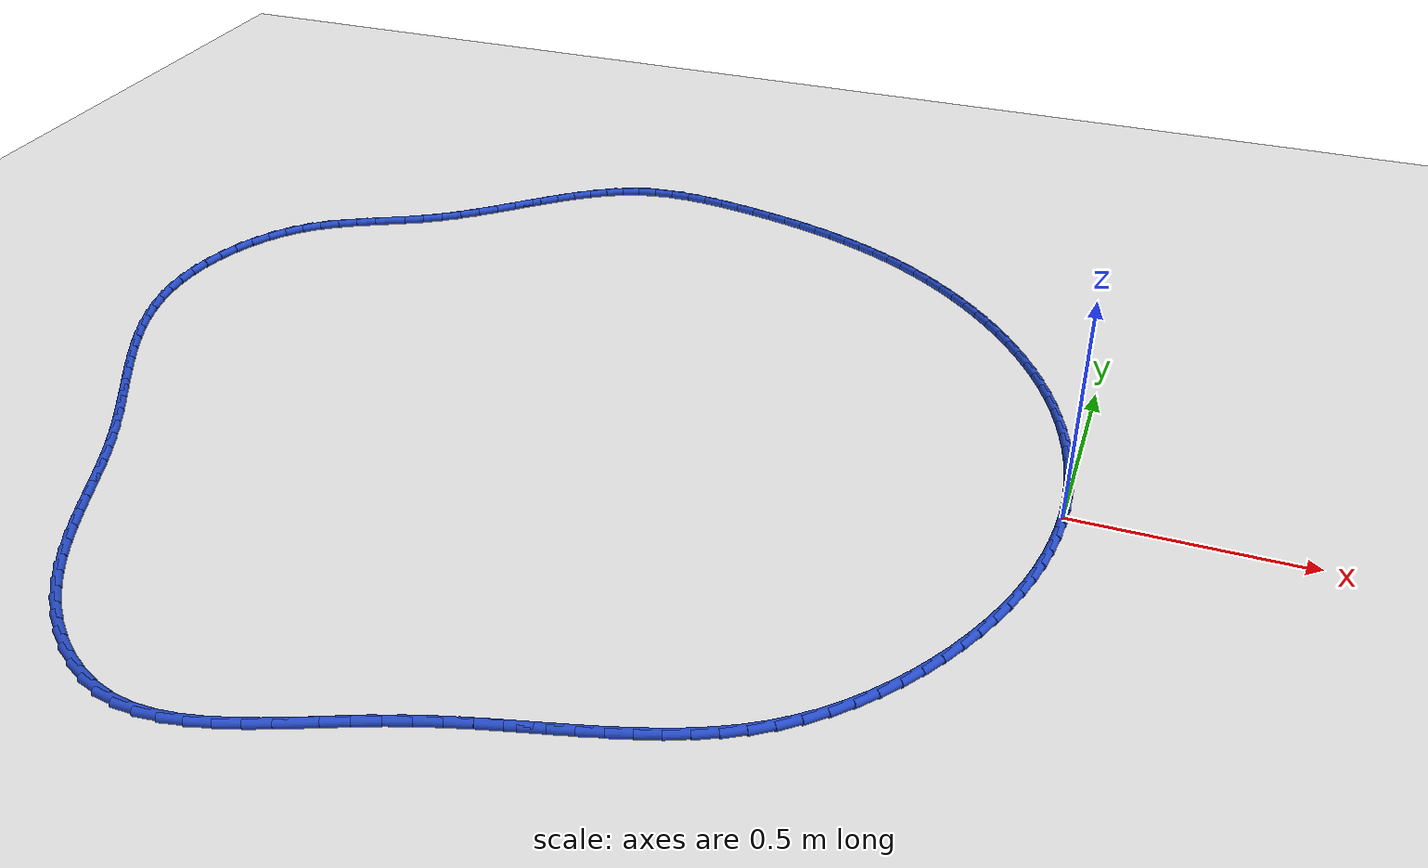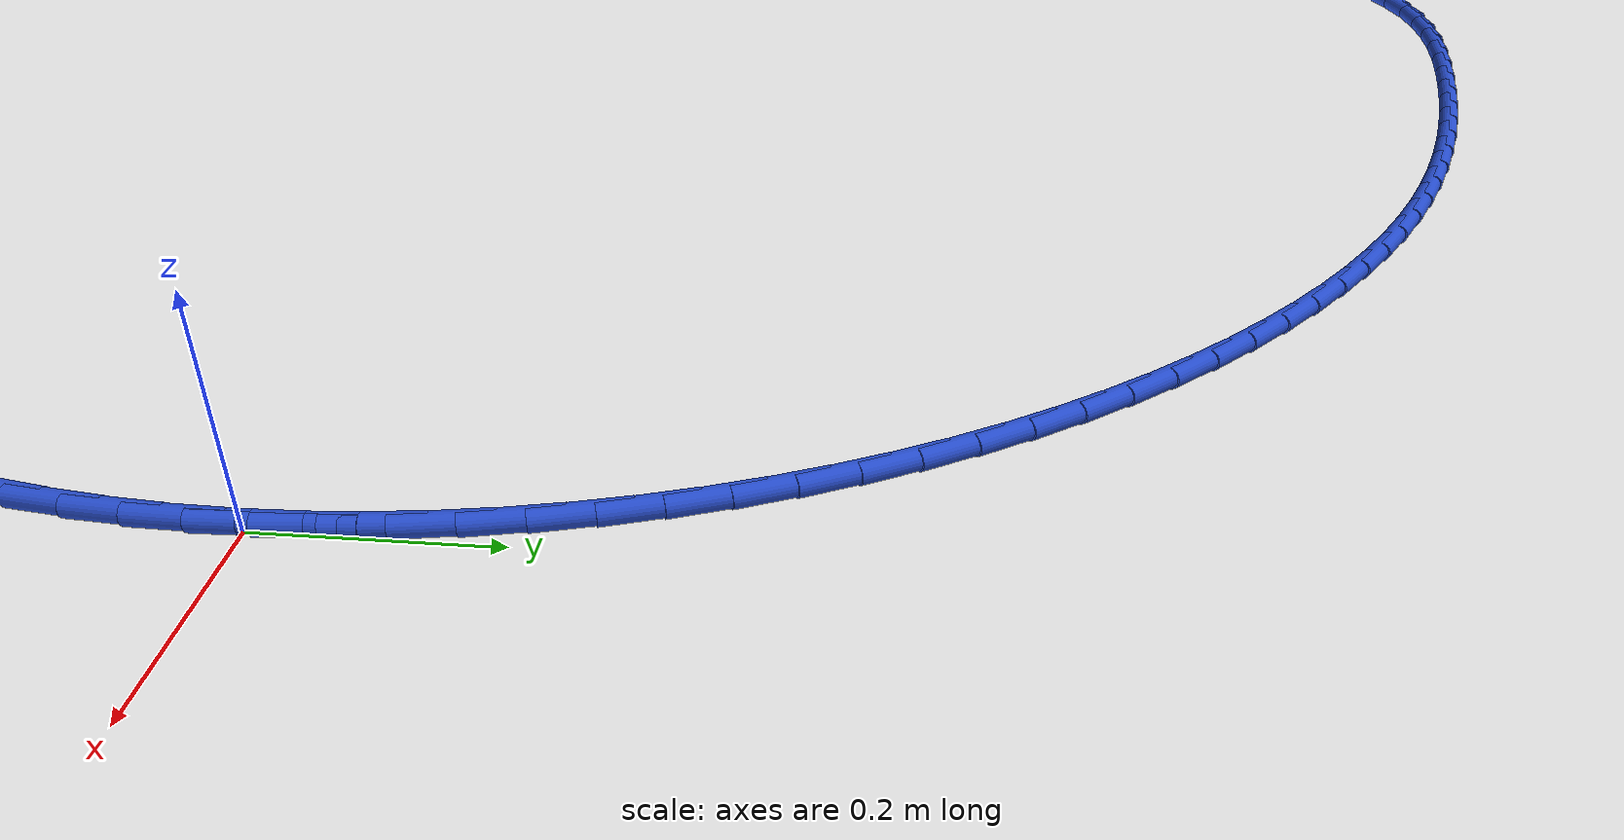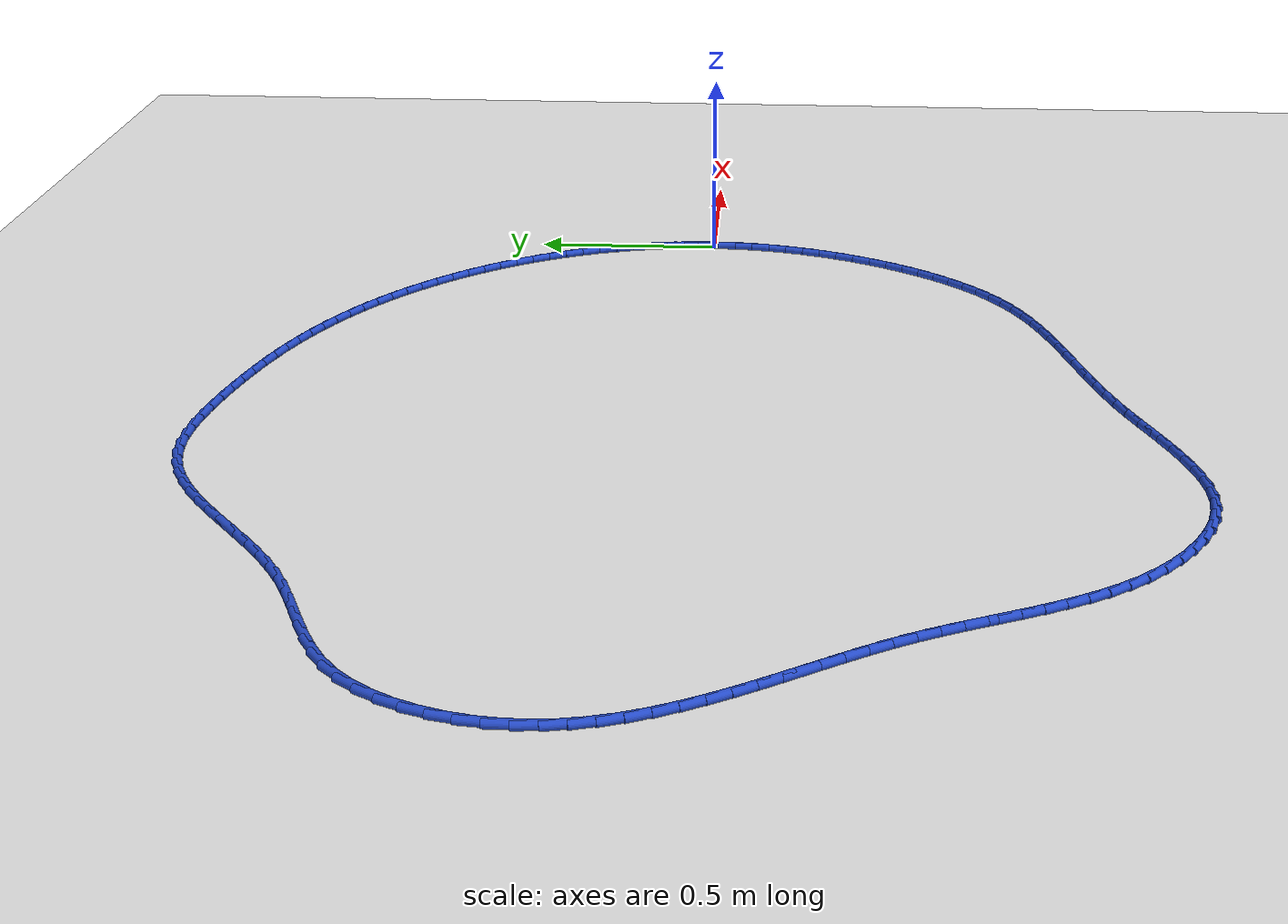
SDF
<sdf version="1.6">
 <world name="default">
  <light name="sun" type="directional">
   <pose>0 0 10 0 -0 0</pose>
   <diffuse>0.8 0.8 0.8 1</diffuse>
   <specular>0.2 0.2 0.2 1</specular>
   <attenuation>
    <range>1000</range>
    <constant>0.9</constant>
    <linear>0.01</linear>
    <quadratic>0.001</quadratic>
   </attenuation>
   <direction>-0.5 0.1 -0.9</direction>
  </light>
  <model name="ground_plane">
   <static>1</static>
   <link name="link">
    <collision name="collision">
     <geometry><plane><normal>0 0 1</normal><size>100 100</size></plane></geometry>
     <surface><friction><ode><mu>100</mu><mu2>50</mu2></ode></friction></surface>
    </collision>
    <visual name="visual">
     <cast_shadows>0</cast_shadows>
     <geometry><plane><normal>0 0 1</normal><size>100 100</size></plane></geometry>
     <material>
      <script><uri>file://media/materials/scripts/gazebo.material</uri><name>Gazebo/WhiteGlow</name></script>
     </material>
    </visual>
   </link>
  </model>
  <gravity>0 0 -9.8</gravity>
  <magnetic_field>6e-06 2.3e-05 -4.2e-05</magnetic_field>
  <atmosphere type="adiabatic"/>
  <physics name="default_physics" default="0" type="ode">
   <max_step_size>0.001</max_step_size>
   <real_time_factor>1</real_time_factor>
   <real_time_update_rate>1000</real_time_update_rate>
  </physics>
  <scene><ambient>0.4 0.4 0.4 1</ambient><background>0.7 0.7 0.7 1</background><shadows>1</shadows></scene>
  <spherical_coordinates>
   <surface_model>EARTH_WGS84</surface_model>
   <latitude_deg>0</latitude_deg>
   <longitude_deg>0</longitude_deg>
   <elevation>0</elevation>
   <heading_deg>0</heading_deg>
  </spherical_coordinates>
  <model name="line">
   <link name="link_0">
    <pose>-1.734723475976807e-18 1.1102230246251565e-16 0.01 0 1.57 -1.542638726486872</pose>
    <collision name="collision">
     <geometry><cylinder><radius>0.01</radius><length>0.08</length></cylinder></geometry>
    </collision>
    <visual name="visual">
     <material>
      <script><name>Gazebo/Blue</name><uri>file://media/materials/scripts/gazebo.material</uri></script>
     </material>
     <geometry><cylinder><radius>0.01</radius><length>0.08</length></cylinder></geometry>
    </visual>
   </link>
   <link name="link_1">
    <pose>-0.0014006014495590987 0.04972835962023079 0.01 0 1.57 -1.4909841500976586</pose>
    <collision name="collision">
     <geometry><cylinder><radius>0.01</radius><length>0.08</length></cylinder></geometry>
    </collision>
    <visual name="visual">
     <material>
      <script><name>Gazebo/Blue</name><uri>file://media/materials/scripts/gazebo.material</uri></script>
     </material>
     <geometry><cylinder><radius>0.01</radius><length>0.08</length></cylinder></geometry>
    </visual>
   </link>
   <link name="link_2">
    <pose>-0.005373536426071804 0.09940117537971081 0.01 0 1.57 -1.440521861142242</pose>
    <collision name="collision">
     <geometry><cylinder><radius>0.01</radius><length>0.08</length></cylinder></geometry>
    </collision>
    <visual name="visual">
     <material>
      <script><name>Gazebo/Blue</name><uri>file://media/materials/scripts/gazebo.material</uri></script>
     </material>
     <geometry><cylinder><radius>0.01</radius><length>0.08</length></cylinder></geometry>
    </visual>
   </link>
   <link name="link_3">
    <pose>-0.011860231685034568 0.14891170272382612 0.01 0 1.57 -1.3911613697983285</pose>
    <collision name="collision">
     <geometry><cylinder><radius>0.01</radius><length>0.08</length></cylinder></geometry>
    </collision>
    <visual name="visual">
     <material>
      <script><name>Gazebo/Blue</name><uri>file://media/materials/scripts/gazebo.material</uri></script>
     </material>
     <geometry><cylinder><radius>0.01</radius><length>0.08</length></cylinder></geometry>
    </visual>
   </link>
   <link name="link_4">
    <pose>-0.020802113981943836 0.19815319709796259 0.01 0 1.57 -1.3427972180517986</pose>
    <collision name="collision">
     <geometry><cylinder><radius>0.01</radius><length>0.08</length></cylinder></geometry>
    </collision>
    <visual name="visual">
     <material>
      <script><name>Gazebo/Blue</name><uri>file://media/materials/scripts/gazebo.material</uri></script>
     </material>
     <geometry><cylinder><radius>0.01</radius><length>0.08</length></cylinder></geometry>
    </visual>
   </link>
   <link name="link_5">
    <pose>-0.03214061007229607 0.24701891394750633 0.01 0 1.57 -1.2953123250698837</pose>
    <collision name="collision">
     <geometry><cylinder><radius>0.01</radius><length>0.08</length></cylinder></geometry>
    </collision>
    <visual name="visual">
     <material>
      <script><name>Gazebo/Blue</name><uri>file://media/materials/scripts/gazebo.material</uri></script>
     </material>
     <geometry><cylinder><radius>0.01</radius><length>0.08</length></cylinder></geometry>
    </visual>
   </link>
   <link name="link_6">
    <pose>-0.045817146711587736 0.2954021087178432 0.01 0 1.57 -1.2485808250050854</pose>
    <collision name="collision">
     <geometry><cylinder><radius>0.01</radius><length>0.08</length></cylinder></geometry>
    </collision>
    <visual name="visual">
     <material>
      <script><name>Gazebo/Blue</name><uri>file://media/materials/scripts/gazebo.material</uri></script>
     </material>
     <geometry><cylinder><radius>0.01</radius><length>0.08</length></cylinder></geometry>
    </visual>
   </link>
   <link name="link_7">
    <pose>-0.06177315065531524 0.3431960368543592 0.01 0 1.57 -1.2024704195762512</pose>
    <collision name="collision">
     <geometry><cylinder><radius>0.01</radius><length>0.08</length></cylinder></geometry>
    </collision>
    <visual name="visual">
     <material>
      <script><name>Gazebo/Blue</name><uri>file://media/materials/scripts/gazebo.material</uri></script>
     </material>
     <geometry><cylinder><radius>0.01</radius><length>0.08</length></cylinder></geometry>
    </visual>
   </link>
   <link name="link_8">
    <pose>-0.0799500486589751 0.39029395380244036 0.01 0 1.57 -1.1568443238065917</pose>
    <collision name="collision">
     <geometry><cylinder><radius>0.01</radius><length>0.08</length></cylinder></geometry>
    </collision>
    <visual name="visual">
     <material>
      <script><name>Gazebo/Blue</name><uri>file://media/materials/scripts/gazebo.material</uri></script>
     </material>
     <geometry><cylinder><radius>0.01</radius><length>0.08</length></cylinder></geometry>
    </visual>
   </link>
   <link name="link_9">
    <pose>-0.10028926653222565 0.4365891161545513 0.01 0 1.57 -1.1117178571968664</pose>
    <collision name="collision">
     <geometry><cylinder><radius>0.01</radius><length>0.08</length></cylinder></geometry>
    </collision>
    <visual name="visual">
     <material>
      <script><name>Gazebo/Blue</name><uri>file://media/materials/scripts/gazebo.material</uri></script>
     </material>
     <geometry><cylinder><radius>0.01</radius><length>0.08</length></cylinder></geometry>
    </visual>
   </link>
   <link name="link_10">
    <pose>-0.12272675383173182 0.4819814219065906 0.01 0 1.57 -1.0674873478157727</pose>
    <collision name="collision">
     <geometry><cylinder><radius>0.01</radius><length>0.08</length></cylinder></geometry>
    </collision>
    <visual name="visual">
     <material>
      <script><name>Gazebo/Blue</name><uri>file://media/materials/scripts/gazebo.material</uri></script>
     </material>
     <geometry><cylinder><radius>0.01</radius><length>0.08</length></cylinder></geometry>
    </visual>
   </link>
   <link name="link_11">
    <pose>-0.14718009467266394 0.5263930420039296 0.01 0 1.57 -1.0241547969968348</pose>
    <collision name="collision">
     <geometry><cylinder><radius>0.01</radius><length>0.08</length></cylinder></geometry>
    </collision>
    <visual name="visual">
     <material>
      <script><name>Gazebo/Blue</name><uri>file://media/materials/scripts/gazebo.material</uri></script>
     </material>
     <geometry><cylinder><radius>0.01</radius><length>0.08</length></cylinder></geometry>
    </visual>
   </link>
   <link name="link_12">
    <pose>-0.17356302752623196 0.569750811251157 0.01 0 1.57 -0.9816073203401003</pose>
    <collision name="collision">
     <geometry><cylinder><radius>0.01</radius><length>0.08</length></cylinder></geometry>
    </collision>
    <visual name="visual">
     <material>
      <script><name>Gazebo/Blue</name><uri>file://media/materials/scripts/gazebo.material</uri></script>
     </material>
     <geometry><cylinder><radius>0.01</radius><length>0.08</length></cylinder></geometry>
    </visual>
   </link>
   <link name="link_13">
    <pose>-0.20178929086364605 0.611981564452862 0.01 0 1.57 -0.9397256333902346</pose>
    <collision name="collision">
     <geometry><cylinder><radius>0.01</radius><length>0.08</length></cylinder></geometry>
    </collision>
    <visual name="visual">
     <material>
      <script><name>Gazebo/Blue</name><uri>file://media/materials/scripts/gazebo.material</uri></script>
     </material>
     <geometry><cylinder><radius>0.01</radius><length>0.08</length></cylinder></geometry>
    </visual>
   </link>
   <link name="link_14">
    <pose>-0.23177262315611633 0.6530121364136338 0.01 0 1.57 -0.8983854272027317</pose>
    <collision name="collision">
     <geometry><cylinder><radius>0.01</radius><length>0.08</length></cylinder></geometry>
    </collision>
    <visual name="visual">
     <material>
      <script><name>Gazebo/Blue</name><uri>file://media/materials/scripts/gazebo.material</uri></script>
     </material>
     <geometry><cylinder><radius>0.01</radius><length>0.08</length></cylinder></geometry>
    </visual>
   </link>
   <link name="link_15">
    <pose>-0.26342676287485295 0.6927693619380614 0.01 0 1.57 -0.8574584037486415</pose>
    <collision name="collision">
     <geometry><cylinder><radius>0.01</radius><length>0.08</length></cylinder></geometry>
    </collision>
    <visual name="visual">
     <material>
      <script><name>Gazebo/Blue</name><uri>file://media/materials/scripts/gazebo.material</uri></script>
     </material>
     <geometry><cylinder><radius>0.01</radius><length>0.08</length></cylinder></geometry>
    </visual>
   </link>
   <link name="link_16">
    <pose>-0.2966654484910659 0.7311800758307337 0.01 0 1.57 -0.8168130265218173</pose>
    <collision name="collision">
     <geometry><cylinder><radius>0.01</radius><length>0.08</length></cylinder></geometry>
    </collision>
    <visual name="visual">
     <material>
      <script><name>Gazebo/Blue</name><uri>file://media/materials/scripts/gazebo.material</uri></script>
     </material>
     <geometry><cylinder><radius>0.01</radius><length>0.08</length></cylinder></geometry>
    </visual>
   </link>
   <link name="link_17">
    <pose>-0.33140241847596535 0.7681711128962402 0.01 0 1.57 -0.7763150450848166</pose>
    <collision name="collision">
     <geometry><cylinder><radius>0.01</radius><length>0.08</length></cylinder></geometry>
    </collision>
    <visual name="visual">
     <material>
      <script><name>Gazebo/Blue</name><uri>file://media/materials/scripts/gazebo.material</uri></script>
     </material>
     <geometry><cylinder><radius>0.01</radius><length>0.08</length></cylinder></geometry>
    </visual>
   </link>
   <link name="link_18">
    <pose>-0.3675514113007613 0.8036693079391697 0.01 0 1.57 -0.7358278538178409</pose>
    <collision name="collision">
     <geometry><cylinder><radius>0.01</radius><length>0.08</length></cylinder></geometry>
    </collision>
    <visual name="visual">
     <material>
      <script><name>Gazebo/Blue</name><uri>file://media/materials/scripts/gazebo.material</uri></script>
     </material>
     <geometry><cylinder><radius>0.01</radius><length>0.08</length></cylinder></geometry>
    </visual>
   </link>
   <link name="link_19">
    <pose>-0.40502616543666403 0.8376014957641111 0.01 0 1.57 -0.6952127462390879</pose>
    <collision name="collision">
     <geometry><cylinder><radius>0.01</radius><length>0.08</length></cylinder></geometry>
    </collision>
    <visual name="visual">
     <material>
      <script><name>Gazebo/Blue</name><uri>file://media/materials/scripts/gazebo.material</uri></script>
     </material>
     <geometry><cylinder><radius>0.01</radius><length>0.08</length></cylinder></geometry>
    </visual>
   </link>
   <link name="link_20">
    <pose>-0.44374041935488356 0.869894511175654 0.01 0 1.57 -0.654329127996041</pose>
    <collision name="collision">
     <geometry><cylinder><radius>0.01</radius><length>0.08</length></cylinder></geometry>
    </collision>
    <visual name="visual">
     <material>
      <script><name>Gazebo/Blue</name><uri>file://media/materials/scripts/gazebo.material</uri></script>
     </material>
     <geometry><cylinder><radius>0.01</radius><length>0.08</length></cylinder></geometry>
    </visual>
   </link>
   <link name="link_21">
    <pose>-0.4836079115266298 0.9004751889783869 0.01 0 1.57 -0.6130347547076476</pose>
    <collision name="collision">
     <geometry><cylinder><radius>0.01</radius><length>0.08</length></cylinder></geometry>
    </collision>
    <visual name="visual">
     <material>
      <script><name>Gazebo/Blue</name><uri>file://media/materials/scripts/gazebo.material</uri></script>
     </material>
     <geometry><cylinder><radius>0.01</radius><length>0.08</length></cylinder></geometry>
    </visual>
   </link>
   <link name="link_22">
    <pose>-0.5245423804231131 0.9292703639768991 0.01 0 1.57 -0.5711860656785848</pose>
    <collision name="collision">
     <geometry><cylinder><radius>0.01</radius><length>0.08</length></cylinder></geometry>
    </collision>
    <visual name="visual">
     <material>
      <script><name>Gazebo/Blue</name><uri>file://media/materials/scripts/gazebo.material</uri></script>
     </material>
     <geometry><cylinder><radius>0.01</radius><length>0.08</length></cylinder></geometry>
    </visual>
   </link>
   <link name="link_23">
    <pose>-0.5664575645155436 0.95620687097578 0.01 0 1.57 -0.5286849295531103</pose>
    <collision name="collision">
     <geometry><cylinder><radius>0.01</radius><length>0.08</length></cylinder></geometry>
    </collision>
    <visual name="visual">
     <material>
      <script><name>Gazebo/Blue</name><uri>file://media/materials/scripts/gazebo.material</uri></script>
     </material>
     <geometry><cylinder><radius>0.01</radius><length>0.08</length></cylinder></geometry>
    </visual>
   </link>
   <link name="link_24">
    <pose>-0.6092687666123695 0.9812151134191898 0.01 0 1.57 -0.4865256813492467</pose>
    <collision name="collision">
     <geometry><cylinder><radius>0.01</radius><length>0.08</length></cylinder></geometry>
    </collision>
    <visual name="visual">
     <material>
      <script><name>Gazebo/Blue</name><uri>file://media/materials/scripts/gazebo.material</uri></script>
     </material>
     <geometry><cylinder><radius>0.01</radius><length>0.08</length></cylinder></geometry>
    </visual>
   </link>
   <link name="link_25">
    <pose>-0.6529272632491425 1.004307559706931 0.01 0 1.57 -0.44595731770965374</pose>
    <collision name="collision">
     <geometry><cylinder><radius>0.01</radius><length>0.08</length></cylinder></geometry>
    </collision>
    <visual name="visual">
     <material>
      <script><name>Gazebo/Blue</name><uri>file://media/materials/scripts/gazebo.material</uri></script>
     </material>
     <geometry><cylinder><radius>0.01</radius><length>0.08</length></cylinder></geometry>
    </visual>
   </link>
   <link name="link_26">
    <pose>-0.6974203013391814 1.0255787355537858 0.01 0 1.57 -0.40725122494489757</pose>
    <collision name="collision">
     <geometry><cylinder><radius>0.01</radius><length>0.08</length></cylinder></geometry>
    </collision>
    <visual name="visual">
     <material>
      <script><name>Gazebo/Blue</name><uri>file://media/materials/scripts/gazebo.material</uri></script>
     </material>
     <geometry><cylinder><radius>0.01</radius><length>0.08</length></cylinder></geometry>
    </visual>
   </link>
   <link name="link_27">
    <pose>-0.7427366914631762 1.0451267337859762 0.01 0 1.57 -0.37059056178817495</pose>
    <collision name="collision">
     <geometry><cylinder><radius>0.01</radius><length>0.08</length></cylinder></geometry>
    </collision>
    <visual name="visual">
     <material>
      <script><name>Gazebo/Blue</name><uri>file://media/materials/scripts/gazebo.material</uri></script>
     </material>
     <geometry><cylinder><radius>0.01</radius><length>0.08</length></cylinder></geometry>
    </visual>
   </link>
   <link name="link_28">
    <pose>-0.7888652442018175 1.0630496472297235 0.01 0 1.57 -0.336116367626109</pose>
    <collision name="collision">
     <geometry><cylinder><radius>0.01</radius><length>0.08</length></cylinder></geometry>
    </collision>
    <visual name="visual">
     <material>
      <script><name>Gazebo/Blue</name><uri>file://media/materials/scripts/gazebo.material</uri></script>
     </material>
     <geometry><cylinder><radius>0.01</radius><length>0.08</length></cylinder></geometry>
    </visual>
   </link>
   <link name="link_29">
    <pose>-0.8357947701357948 1.0794455687112487 0.01 0 1.57 -0.30392955717776515</pose>
    <collision name="collision">
     <geometry><cylinder><radius>0.01</radius><length>0.08</length></cylinder></geometry>
    </collision>
    <visual name="visual">
     <material>
      <script><name>Gazebo/Blue</name><uri>file://media/materials/scripts/gazebo.material</uri></script>
     </material>
     <geometry><cylinder><radius>0.01</radius><length>0.08</length></cylinder></geometry>
    </visual>
   </link>
   <link name="link_30">
    <pose>-0.8835140798457987 1.0944125910567741 0.01 0 1.57 -0.27409446702823836</pose>
    <collision name="collision">
     <geometry><cylinder><radius>0.01</radius><length>0.08</length></cylinder></geometry>
    </collision>
    <visual name="visual">
     <material>
      <script><name>Gazebo/Blue</name><uri>file://media/materials/scripts/gazebo.material</uri></script>
     </material>
     <geometry><cylinder><radius>0.01</radius><length>0.08</length></cylinder></geometry>
    </visual>
   </link>
   <link name="link_31">
    <pose>-0.9320119839125185 1.10804880709252 0.01 0 1.57 -0.24664338667362207</pose>
    <collision name="collision">
     <geometry><cylinder><radius>0.01</radius><length>0.08</length></cylinder></geometry>
    </collision>
    <visual name="visual">
     <material>
      <script><name>Gazebo/Blue</name><uri>file://media/materials/scripts/gazebo.material</uri></script>
     </material>
     <geometry><cylinder><radius>0.01</radius><length>0.08</length></cylinder></geometry>
    </visual>
   </link>
   <link name="link_32">
    <pose>-0.9812772929166451 1.1204523096447092 0.01 0 1.57 -0.22158155939954238</pose>
    <collision name="collision">
     <geometry><cylinder><radius>0.01</radius><length>0.08</length></cylinder></geometry>
    </collision>
    <visual name="visual">
     <material>
      <script><name>Gazebo/Blue</name><uri>file://media/materials/scripts/gazebo.material</uri></script>
     </material>
     <geometry><cylinder><radius>0.01</radius><length>0.08</length></cylinder></geometry>
    </visual>
   </link>
   <link name="link_33">
    <pose>-1.0312988174388684 1.1317211915395622 0.01 0 1.57 -0.1980277975267282</pose>
    <collision name="collision">
     <geometry><cylinder><radius>0.01</radius><length>0.08</length></cylinder></geometry>
    </collision>
    <visual name="visual">
     <material>
      <script><name>Gazebo/Blue</name><uri>file://media/materials/scripts/gazebo.material</uri></script>
     </material>
     <geometry><cylinder><radius>0.01</radius><length>0.08</length></cylinder></geometry>
    </visual>
   </link>
   <link name="link_34">
    <pose>-1.0820385991693624 1.141902514895077 0.01 0 1.57 -0.16665743385439394</pose>
    <collision name="collision">
     <geometry><cylinder><radius>0.01</radius><length>0.08</length></cylinder></geometry>
    </collision>
    <visual name="visual">
     <material>
      <script><name>Gazebo/Blue</name><uri>file://media/materials/scripts/gazebo.material</uri></script>
     </material>
     <geometry><cylinder><radius>0.01</radius><length>0.08</length></cylinder></geometry>
    </visual>
   </link>
   <link name="link_35">
    <pose>-1.1331761582934659 1.150504758712714 0.01 0 1.57 -0.1210321985497209</pose>
    <collision name="collision">
     <geometry><cylinder><radius>0.01</radius><length>0.08</length></cylinder></geometry>
    </collision>
    <visual name="visual">
     <material>
      <script><name>Gazebo/Blue</name><uri>file://media/materials/scripts/gazebo.material</uri></script>
     </material>
     <geometry><cylinder><radius>0.01</radius><length>0.08</length></cylinder></geometry>
    </visual>
   </link>
   <link name="link_36">
    <pose>-1.1842214919961074 1.1567132328746879 0.01 0 1.57 -0.059295734067460776</pose>
    <collision name="collision">
     <geometry><cylinder><radius>0.01</radius><length>0.08</length></cylinder></geometry>
    </collision>
    <visual name="visual">
     <material>
      <script><name>Gazebo/Blue</name><uri>file://media/materials/scripts/gazebo.material</uri></script>
     </material>
     <geometry><cylinder><radius>0.01</radius><length>0.08</length></cylinder></geometry>
    </visual>
   </link>
   <link name="link_37">
    <pose>-1.234682293336803 1.1597088548080403 0.01 0 1.57 0.020981726617493562</pose>
    <collision name="collision">
     <geometry><cylinder><radius>0.01</radius><length>0.08</length></cylinder></geometry>
    </collision>
    <visual name="visual">
     <material>
      <script><name>Gazebo/Blue</name><uri>file://media/materials/scripts/gazebo.material</uri></script>
     </material>
     <geometry><cylinder><radius>0.01</radius><length>0.08</length></cylinder></geometry>
    </visual>
   </link>
   <link name="link_38">
    <pose>-1.2840662553750672 1.1586725419398116 0.01 0 1.57 0.12251111647595986</pose>
    <collision name="collision">
     <geometry><cylinder><radius>0.01</radius><length>0.08</length></cylinder></geometry>
    </collision>
    <visual name="visual">
     <material>
      <script><name>Gazebo/Blue</name><uri>file://media/materials/scripts/gazebo.material</uri></script>
     </material>
     <geometry><cylinder><radius>0.01</radius><length>0.08</length></cylinder></geometry>
    </visual>
   </link>
   <link name="link_39">
    <pose>-1.3318810711704174 1.1527852116970432 0.01 0 1.57 0.24687481921970103</pose>
    <collision name="collision">
     <geometry><cylinder><radius>0.01</radius><length>0.08</length></cylinder></geometry>
    </collision>
    <visual name="visual">
     <material>
      <script><name>Gazebo/Blue</name><uri>file://media/materials/scripts/gazebo.material</uri></script>
     </material>
     <geometry><cylinder><radius>0.01</radius><length>0.08</length></cylinder></geometry>
    </visual>
   </link>
   <link name="link_40">
    <pose>-1.3776468200733747 1.1412515279409419 0.01 0 1.57 0.37683864485815727</pose>
    <collision name="collision">
     <geometry><cylinder><radius>0.01</radius><length>0.08</length></cylinder></geometry>
    </collision>
    <visual name="visual">
     <material>
      <script><name>Gazebo/Blue</name><uri>file://media/materials/scripts/gazebo.material</uri></script>
     </material>
     <geometry><cylinder><radius>0.01</radius><length>0.08</length></cylinder></geometry>
    </visual>
   </link>
   <link name="link_41">
    <pose>-1.4212572904974448 1.1239926125633306 0.01 0 1.57 0.48910395518948574</pose>
    <collision name="collision">
     <geometry><cylinder><radius>0.01</radius><length>0.08</length></cylinder></geometry>
    </collision>
    <visual name="visual">
     <material>
      <script><name>Gazebo/Blue</name><uri>file://media/materials/scripts/gazebo.material</uri></script>
     </material>
     <geometry><cylinder><radius>0.01</radius><length>0.08</length></cylinder></geometry>
    </visual>
   </link>
   <link name="link_42">
    <pose>-1.4630372095517772 1.101755763537329 0.01 0 1.57 0.5803415601344453</pose>
    <collision name="collision">
     <geometry><cylinder><radius>0.01</radius><length>0.08</length></cylinder></geometry>
    </collision>
    <visual name="visual">
     <material>
      <script><name>Gazebo/Blue</name><uri>file://media/materials/scripts/gazebo.material</uri></script>
     </material>
     <geometry><cylinder><radius>0.01</radius><length>0.08</length></cylinder></geometry>
    </visual>
   </link>
   <link name="link_43">
    <pose>-1.5033352094601888 1.0753341086354113 0.01 0 1.57 0.650649305920409</pose>
    <collision name="collision">
     <geometry><cylinder><radius>0.01</radius><length>0.08</length></cylinder></geometry>
    </collision>
    <visual name="visual">
     <material>
      <script><name>Gazebo/Blue</name><uri>file://media/materials/scripts/gazebo.material</uri></script>
     </material>
     <geometry><cylinder><radius>0.01</radius><length>0.08</length></cylinder></geometry>
    </visual>
   </link>
   <link name="link_44">
    <pose>-1.542499922446493 1.0455207756300502 0.01 0 1.57 0.7012911979180595</pose>
    <collision name="collision">
     <geometry><cylinder><radius>0.01</radius><length>0.08</length></cylinder></geometry>
    </collision>
    <visual name="visual">
     <material>
      <script><name>Gazebo/Blue</name><uri>file://media/materials/scripts/gazebo.material</uri></script>
     </material>
     <geometry><cylinder><radius>0.01</radius><length>0.08</length></cylinder></geometry>
    </visual>
   </link>
   <link name="link_45">
    <pose>-1.5808799807345038 1.0131088922937184 0.01 0 1.57 0.7337995944201634</pose>
    <collision name="collision">
     <geometry><cylinder><radius>0.01</radius><length>0.08</length></cylinder></geometry>
    </collision>
    <visual name="visual">
     <material>
      <script><name>Gazebo/Blue</name><uri>file://media/materials/scripts/gazebo.material</uri></script>
     </material>
     <geometry><cylinder><radius>0.01</radius><length>0.08</length></cylinder></geometry>
    </visual>
   </link>
   <link name="link_46">
    <pose>-1.6188240165480363 0.9788915863988884 0.01 0 1.57 0.7494691820974768</pose>
    <collision name="collision">
     <geometry><cylinder><radius>0.01</radius><length>0.08</length></cylinder></geometry>
    </collision>
    <visual name="visual">
     <material>
      <script><name>Gazebo/Blue</name><uri>file://media/materials/scripts/gazebo.material</uri></script>
     </material>
     <geometry><cylinder><radius>0.01</radius><length>0.08</length></cylinder></geometry>
    </visual>
   </link>
   <link name="link_47">
    <pose>-1.6566806621109031 0.943661985718034 0.01 0 1.57 0.7491324179359471</pose>
    <collision name="collision">
     <geometry><cylinder><radius>0.01</radius><length>0.08</length></cylinder></geometry>
    </collision>
    <visual name="visual">
     <material>
      <script><name>Gazebo/Blue</name><uri>file://media/materials/scripts/gazebo.material</uri></script>
     </material>
     <geometry><cylinder><radius>0.01</radius><length>0.08</length></cylinder></geometry>
    </visual>
   </link>
   <link name="link_48">
    <pose>-1.6947985496469204 0.9082132180236276 0.01 0 1.57 0.7330977995031656</pose>
    <collision name="collision">
     <geometry><cylinder><radius>0.01</radius><length>0.08</length></cylinder></geometry>
    </collision>
    <visual name="visual">
     <material>
      <script><name>Gazebo/Blue</name><uri>file://media/materials/scripts/gazebo.material</uri></script>
     </material>
     <geometry><cylinder><radius>0.01</radius><length>0.08</length></cylinder></geometry>
    </visual>
   </link>
   <link name="link_49">
    <pose>-1.7335263113799018 0.8733384110881426 0.01 0 1.57 0.7011844575428977</pose>
    <collision name="collision">
     <geometry><cylinder><radius>0.01</radius><length>0.08</length></cylinder></geometry>
    </collision>
    <visual name="visual">
     <material>
      <script><name>Gazebo/Blue</name><uri>file://media/materials/scripts/gazebo.material</uri></script>
     </material>
     <geometry><cylinder><radius>0.01</radius><length>0.08</length></cylinder></geometry>
    </visual>
   </link>
   <link name="link_50">
    <pose>-1.7732125795336606 0.8398306926840513 0.01 0 1.57 0.6528405167930271</pose>
    <collision name="collision">
     <geometry><cylinder><radius>0.01</radius><length>0.08</length></cylinder></geometry>
    </collision>
    <visual name="visual">
     <material>
      <script><name>Gazebo/Blue</name><uri>file://media/materials/scripts/gazebo.material</uri></script>
     </material>
     <geometry><cylinder><radius>0.01</radius><length>0.08</length></cylinder></geometry>
    </visual>
   </link>
   <link name="link_51">
    <pose>-1.814205986332012 0.8084831905838271 0.01 0 1.57 0.5874332893839208</pose>
    <collision name="collision">
     <geometry><cylinder><radius>0.01</radius><length>0.08</length></cylinder></geometry>
    </collision>
    <visual name="visual">
     <material>
      <script><name>Gazebo/Blue</name><uri>file://media/materials/scripts/gazebo.material</uri></script>
     </material>
     <geometry><cylinder><radius>0.01</radius><length>0.08</length></cylinder></geometry>
    </visual>
   </link>
   <link name="link_52">
    <pose>-1.856853651818118 0.7800864712865497 0.01 0 1.57 0.5179578473718071</pose>
    <collision name="collision">
     <geometry><cylinder><radius>0.01</radius><length>0.08</length></cylinder></geometry>
    </collision>
    <visual name="visual">
     <material>
      <script><name>Gazebo/Blue</name><uri>file://media/materials/scripts/gazebo.material</uri></script>
     </material>
     <geometry><cylinder><radius>0.01</radius><length>0.08</length></cylinder></geometry>
    </visual>
   </link>
   <link name="link_53">
    <pose>-1.9011545633953706 0.7548414476240647 0.01 0 1.57 0.47510370564622567</pose>
    <collision name="collision">
     <geometry><cylinder><radius>0.01</radius><length>0.08</length></cylinder></geometry>
    </collision>
    <visual name="visual">
     <material>
      <script><name>Gazebo/Blue</name><uri>file://media/materials/scripts/gazebo.material</uri></script>
     </material>
     <geometry><cylinder><radius>0.01</radius><length>0.08</length></cylinder></geometry>
    </visual>
   </link>
   <link name="link_54">
    <pose>-1.9463169920493928 0.731609747390791 0.01 0 1.57 0.46329614184088624</pose>
    <collision name="collision">
     <geometry><cylinder><radius>0.01</radius><length>0.08</length></cylinder></geometry>
    </collision>
    <visual name="visual">
     <material>
      <script><name>Gazebo/Blue</name><uri>file://media/materials/scripts/gazebo.material</uri></script>
     </material>
     <geometry><cylinder><radius>0.01</radius><length>0.08</length></cylinder></geometry>
    </visual>
   </link>
   <link name="link_55">
    <pose>-1.9914400178842462 0.7090680550682078 0.01 0 1.57 0.4830757617602121</pose>
    <collision name="collision">
     <geometry><cylinder><radius>0.01</radius><length>0.08</length></cylinder></geometry>
    </collision>
    <visual name="visual">
     <material>
      <script><name>Gazebo/Blue</name><uri>file://media/materials/scripts/gazebo.material</uri></script>
     </material>
     <geometry><cylinder><radius>0.01</radius><length>0.08</length></cylinder></geometry>
    </visual>
   </link>
   <link name="link_56">
    <pose>-2.035622721003991 0.6858930551377941 0.01 0 1.57 0.5356607207719337</pose>
    <collision name="collision">
     <geometry><cylinder><radius>0.01</radius><length>0.08</length></cylinder></geometry>
    </collision>
    <visual name="visual">
     <material>
      <script><name>Gazebo/Blue</name><uri>file://media/materials/scripts/gazebo.material</uri></script>
     </material>
     <geometry><cylinder><radius>0.01</radius><length>0.08</length></cylinder></geometry>
    </visual>
   </link>
   <link name="link_57">
    <pose>-2.0779641815126886 0.6607614320810288 0.01 0 1.57 0.6223590494526726</pose>
    <collision name="collision">
     <geometry><cylinder><radius>0.01</radius><length>0.08</length></cylinder></geometry>
    </collision>
    <visual name="visual">
     <material>
      <script><name>Gazebo/Blue</name><uri>file://media/materials/scripts/gazebo.material</uri></script>
     </material>
     <geometry><cylinder><radius>0.01</radius><length>0.08</length></cylinder></geometry>
    </visual>
   </link>
   <link name="link_58">
    <pose>-2.1175634795143994 0.6323498703793914 0.01 0 1.57 0.7424584884439164</pose>
    <collision name="collision">
     <geometry><cylinder><radius>0.01</radius><length>0.08</length></cylinder></geometry>
    </collision>
    <visual name="visual">
     <material>
      <script><name>Gazebo/Blue</name><uri>file://media/materials/scripts/gazebo.material</uri></script>
     </material>
     <geometry><cylinder><radius>0.01</radius><length>0.08</length></cylinder></geometry>
    </visual>
   </link>
   <link name="link_59">
    <pose>-2.1535255914380613 0.5993507525416252 0.01 0 1.57 0.8756506572910439</pose>
    <collision name="collision">
     <geometry><cylinder><radius>0.01</radius><length>0.08</length></cylinder></geometry>
    </collision>
    <visual name="visual">
     <material>
      <script><name>Gazebo/Blue</name><uri>file://media/materials/scripts/gazebo.material</uri></script>
     </material>
     <geometry><cylinder><radius>0.01</radius><length>0.08</length></cylinder></geometry>
    </visual>
   </link>
   <link name="link_60">
    <pose>-2.1852687615727504 0.561290486933776 0.01 0 1.57 0.9965549942717626</pose>
    <collision name="collision">
     <geometry><cylinder><radius>0.01</radius><length>0.08</length></cylinder></geometry>
    </collision>
    <visual name="visual">
     <material>
      <script><name>Gazebo/Blue</name><uri>file://media/materials/scripts/gazebo.material</uri></script>
     </material>
     <geometry><cylinder><radius>0.01</radius><length>0.08</length></cylinder></geometry>
    </visual>
   </link>
   <link name="link_61">
    <pose>-2.2126748358751938 0.5189297476334631 0.01 0 1.57 1.1056165719106248</pose>
    <collision name="collision">
     <geometry><cylinder><radius>0.01</radius><length>0.08</length></cylinder></geometry>
    </collision>
    <visual name="visual">
     <material>
      <script><name>Gazebo/Blue</name><uri>file://media/materials/scripts/gazebo.material</uri></script>
     </material>
     <geometry><cylinder><radius>0.01</radius><length>0.08</length></cylinder></geometry>
    </visual>
   </link>
   <link name="link_62">
    <pose>-2.235663079040139 0.47312883015742646 0.01 0 1.57 1.205754740752293</pose>
    <collision name="collision">
     <geometry><cylinder><radius>0.01</radius><length>0.08</length></cylinder></geometry>
    </collision>
    <visual name="visual">
     <material>
      <script><name>Gazebo/Blue</name><uri>file://media/materials/scripts/gazebo.material</uri></script>
     </material>
     <geometry><cylinder><radius>0.01</radius><length>0.08</length></cylinder></geometry>
    </visual>
   </link>
   <link name="link_63">
    <pose>-2.2541527557623344 0.42474803002240513 0.01 0 1.57 1.29996805966682</pose>
    <collision name="collision">
     <geometry><cylinder><radius>0.01</radius><length>0.08</length></cylinder></geometry>
    </collision>
    <visual name="visual">
     <material>
      <script><name>Gazebo/Blue</name><uri>file://media/materials/scripts/gazebo.material</uri></script>
     </material>
     <geometry><cylinder><radius>0.01</radius><length>0.08</length></cylinder></geometry>
    </visual>
   </link>
   <link name="link_64">
    <pose>-2.268063130736526 0.37464764274513906 0.01 0 1.57 1.3912288793765015</pose>
    <collision name="collision">
     <geometry><cylinder><radius>0.01</radius><length>0.08</length></cylinder></geometry>
    </collision>
    <visual name="visual">
     <material>
      <script><name>Gazebo/Blue</name><uri>file://media/materials/scripts/gazebo.material</uri></script>
     </material>
     <geometry><cylinder><radius>0.01</radius><length>0.08</length></cylinder></geometry>
    </visual>
   </link>
   <link name="link_65">
    <pose>-2.2773134686574643 0.3236879638423676 0.01 0 1.57 1.4825316953811323</pose>
    <collision name="collision">
     <geometry><cylinder><radius>0.01</radius><length>0.08</length></cylinder></geometry>
    </collision>
    <visual name="visual">
     <material>
      <script><name>Gazebo/Blue</name><uri>file://media/materials/scripts/gazebo.material</uri></script>
     </material>
     <geometry><cylinder><radius>0.01</radius><length>0.08</length></cylinder></geometry>
    </visual>
   </link>
   <link name="link_66">
    <pose>-2.281823034219897 0.27272928883082986 0.01 0 1.57 -1.5650537961055717</pose>
    <collision name="collision">
     <geometry><cylinder><radius>0.01</radius><length>0.08</length></cylinder></geometry>
    </collision>
    <visual name="visual">
     <material>
      <script><name>Gazebo/Blue</name><uri>file://media/materials/scripts/gazebo.material</uri></script>
     </material>
     <geometry><cylinder><radius>0.01</radius><length>0.08</length></cylinder></geometry>
    </visual>
   </link>
   <link name="link_67">
    <pose>-2.2815350876772875 0.22258704440782182 0.01 0 1.57 -1.4723032508969647</pose>
    <collision name="collision">
     <geometry><cylinder><radius>0.01</radius><length>0.08</length></cylinder></geometry>
    </collision>
    <visual name="visual">
     <material>
      <script><name>Gazebo/Blue</name><uri>file://media/materials/scripts/gazebo.material</uri></script>
     </material>
     <geometry><cylinder><radius>0.01</radius><length>0.08</length></cylinder></geometry>
    </visual>
   </link>
   <link name="link_68">
    <pose>-2.276687251434488 0.17352623532062134 0.01 0 1.57 -1.38631401132237</pose>
    <collision name="collision">
     <geometry><cylinder><radius>0.01</radius><length>0.08</length></cylinder></geometry>
    </collision>
    <visual name="visual">
     <material>
      <script><name>Gazebo/Blue</name><uri>file://media/materials/scripts/gazebo.material</uri></script>
     </material>
     <geometry><cylinder><radius>0.01</radius><length>0.08</length></cylinder></geometry>
    </visual>
   </link>
   <link name="link_69">
    <pose>-2.2677146438621065 0.12544257252624227 0.01 0 1.57 -1.3088648517512105</pose>
    <collision name="collision">
     <geometry><cylinder><radius>0.01</radius><length>0.08</length></cylinder></geometry>
    </collision>
    <visual name="visual">
     <material>
      <script><name>Gazebo/Blue</name><uri>file://media/materials/scripts/gazebo.material</uri></script>
     </material>
     <geometry><cylinder><radius>0.01</radius><length>0.08</length></cylinder></geometry>
    </visual>
   </link>
   <link name="link_70">
    <pose>-2.2550560331128415 0.07822494232654527 0.01 0 1.57 -1.2409656220218708</pose>
    <collision name="collision">
     <geometry><cylinder><radius>0.01</radius><length>0.08</length></cylinder></geometry>
    </collision>
    <visual name="visual">
     <material>
      <script><name>Gazebo/Blue</name><uri>file://media/materials/scripts/gazebo.material</uri></script>
     </material>
     <geometry><cylinder><radius>0.01</radius><length>0.08</length></cylinder></geometry>
    </visual>
   </link>
   <link name="link_71">
    <pose>-2.2391501873393866 0.03176223102339205 0.01 0 1.57 -1.1830346060396248</pose>
    <collision name="collision">
     <geometry><cylinder><radius>0.01</radius><length>0.08</length></cylinder></geometry>
    </collision>
    <visual name="visual">
     <material>
      <script><name>Gazebo/Blue</name><uri>file://media/materials/scripts/gazebo.material</uri></script>
     </material>
     <geometry><cylinder><radius>0.01</radius><length>0.08</length></cylinder></geometry>
    </visual>
   </link>
   <link name="link_72">
    <pose>-2.220435874694441 -0.014056675081356574 0.01 0 1.57 -1.1350681250014132</pose>
    <collision name="collision">
     <geometry><cylinder><radius>0.01</radius><length>0.08</length></cylinder></geometry>
    </collision>
    <visual name="visual">
     <material>
      <script><name>Gazebo/Blue</name><uri>file://media/materials/scripts/gazebo.material</uri></script>
     </material>
     <geometry><cylinder><radius>0.01</radius><length>0.08</length></cylinder></geometry>
    </visual>
   </link>
   <link name="link_73">
    <pose>-2.1993518633306994 -0.059342889685839964 0.01 0 1.57 -1.0968137701040288</pose>
    <collision name="collision">
     <geometry><cylinder><radius>0.01</radius><length>0.08</length></cylinder></geometry>
    </collision>
    <visual name="visual">
     <material>
      <script><name>Gazebo/Blue</name><uri>file://media/materials/scripts/gazebo.material</uri></script>
     </material>
     <geometry><cylinder><radius>0.01</radius><length>0.08</length></cylinder></geometry>
    </visual>
   </link>
   <link name="link_74">
    <pose>-2.1763369214008588 -0.10420752648819559 0.01 0 1.57 -1.0679133220263883</pose>
    <collision name="collision">
     <geometry><cylinder><radius>0.01</radius><length>0.08</length></cylinder></geometry>
    </collision>
    <visual name="visual">
     <material>
      <script><name>Gazebo/Blue</name><uri>file://media/materials/scripts/gazebo.material</uri></script>
     </material>
     <geometry><cylinder><radius>0.01</radius><length>0.08</length></cylinder></geometry>
    </visual>
   </link>
   <link name="link_75">
    <pose>-2.1518298170576142 -0.14876169918656296 0.01 0 1.57 -1.0480056752352673</pose>
    <collision name="collision">
     <geometry><cylinder><radius>0.01</radius><length>0.08</length></cylinder></geometry>
    </collision>
    <visual name="visual">
     <material>
      <script><name>Gazebo/Blue</name><uri>file://media/materials/scripts/gazebo.material</uri></script>
     </material>
     <geometry><cylinder><radius>0.01</radius><length>0.08</length></cylinder></geometry>
    </visual>
   </link>
   <link name="link_76">
    <pose>-2.1262693184536645 -0.1931165214790809 0.01 0 1.57 -1.0367935465985996</pose>
    <collision name="collision">
     <geometry><cylinder><radius>0.01</radius><length>0.08</length></cylinder></geometry>
    </collision>
    <visual name="visual">
     <material>
      <script><name>Gazebo/Blue</name><uri>file://media/materials/scripts/gazebo.material</uri></script>
     </material>
     <geometry><cylinder><radius>0.01</radius><length>0.08</length></cylinder></geometry>
    </visual>
   </link>
   <link name="link_77">
    <pose>-2.100094193741704 -0.23738310706388818 0.01 0 1.57 -1.0340822119709623</pose>
    <collision name="collision">
     <geometry><cylinder><radius>0.01</radius><length>0.08</length></cylinder></geometry>
    </collision>
    <visual name="visual">
     <material>
      <script><name>Gazebo/Blue</name><uri>file://media/materials/scripts/gazebo.material</uri></script>
     </material>
     <geometry><cylinder><radius>0.01</radius><length>0.08</length></cylinder></geometry>
    </visual>
   </link>
   <link name="link_78">
    <pose>-2.073743211074429 -0.28167256963912435 0.01 0 1.57 -1.0397978922952544</pose>
    <collision name="collision">
     <geometry><cylinder><radius>0.01</radius><length>0.08</length></cylinder></geometry>
    </collision>
    <visual name="visual">
     <material>
      <script><name>Gazebo/Blue</name><uri>file://media/materials/scripts/gazebo.material</uri></script>
     </material>
     <geometry><cylinder><radius>0.01</radius><length>0.08</length></cylinder></geometry>
    </visual>
   </link>
   <link name="link_79">
    <pose>-2.047655138604537 -0.3260960229029267 0.01 0 1.57 -1.0539906528156404</pose>
    <collision name="collision">
     <geometry><cylinder><radius>0.01</radius><length>0.08</length></cylinder></geometry>
    </collision>
    <visual name="visual">
     <material>
      <script><name>Gazebo/Blue</name><uri>file://media/materials/scripts/gazebo.material</uri></script>
     </material>
     <geometry><cylinder><radius>0.01</radius><length>0.08</length></cylinder></geometry>
    </visual>
   </link>
   <link name="link_80">
    <pose>-2.022268744484724 -0.3707645805534351 0.01 0 1.57 -1.0768233188146168</pose>
    <collision name="collision">
     <geometry><cylinder><radius>0.01</radius><length>0.08</length></cylinder></geometry>
    </collision>
    <visual name="visual">
     <material>
      <script><name>Gazebo/Blue</name><uri>file://media/materials/scripts/gazebo.material</uri></script>
     </material>
     <geometry><cylinder><radius>0.01</radius><length>0.08</length></cylinder></geometry>
    </visual>
   </link>
   <link name="link_81">
    <pose>-1.9980227968676858 -0.4157893562887878 0.01 0 1.57 -1.1083896287668777</pose>
    <collision name="collision">
     <geometry><cylinder><radius>0.01</radius><length>0.08</length></cylinder></geometry>
    </collision>
    <visual name="visual">
     <material>
      <script><name>Gazebo/Blue</name><uri>file://media/materials/scripts/gazebo.material</uri></script>
     </material>
     <geometry><cylinder><radius>0.01</radius><length>0.08</length></cylinder></geometry>
    </visual>
   </link>
   <link name="link_82">
    <pose>-1.9753485107658948 -0.46127896243802124 0.01 0 1.57 -1.1413392504001236</pose>
    <collision name="collision">
     <geometry><cylinder><radius>0.01</radius><length>0.08</length></cylinder></geometry>
    </collision>
    <visual name="visual">
     <material>
      <script><name>Gazebo/Blue</name><uri>file://media/materials/scripts/gazebo.material</uri></script>
     </material>
     <geometry><cylinder><radius>0.01</radius><length>0.08</length></cylinder></geometry>
    </visual>
   </link>
   <link name="link_83">
    <pose>-1.9543091016571397 -0.5072201411359454 0.01 0 1.57 -1.164712441393673</pose>
    <collision name="collision">
     <geometry><cylinder><radius>0.01</radius><length>0.08</length></cylinder></geometry>
    </collision>
    <visual name="visual">
     <material>
      <script><name>Gazebo/Blue</name><uri>file://media/materials/scripts/gazebo.material</uri></script>
     </material>
     <geometry><cylinder><radius>0.01</radius><length>0.08</length></cylinder></geometry>
    </visual>
   </link>
   <link name="link_84">
    <pose>-1.9344416224906709 -0.5534253855754506 0.01 0 1.57 -1.177471022953458</pose>
    <collision name="collision">
     <geometry><cylinder><radius>0.01</radius><length>0.08</length></cylinder></geometry>
    </collision>
    <visual name="visual">
     <material>
      <script><name>Gazebo/Blue</name><uri>file://media/materials/scripts/gazebo.material</uri></script>
     </material>
     <geometry><cylinder><radius>0.01</radius><length>0.08</length></cylinder></geometry>
    </visual>
   </link>
   <link name="link_85">
    <pose>-1.9152426674523537 -0.5996937902440288 0.01 0 1.57 -1.1794692409208791</pose>
    <collision name="collision">
     <geometry><cylinder><radius>0.01</radius><length>0.08</length></cylinder></geometry>
    </collision>
    <visual name="visual">
     <material>
      <script><name>Gazebo/Blue</name><uri>file://media/materials/scripts/gazebo.material</uri></script>
     </material>
     <geometry><cylinder><radius>0.01</radius><length>0.08</length></cylinder></geometry>
    </visual>
   </link>
   <link name="link_86">
    <pose>-1.8962088307280514 -0.6458244496291708 0.01 0 1.57 -1.1705819325126863</pose>
    <collision name="collision">
     <geometry><cylinder><radius>0.01</radius><length>0.08</length></cylinder></geometry>
    </collision>
    <visual name="visual">
     <material>
      <script><name>Gazebo/Blue</name><uri>file://media/materials/scripts/gazebo.material</uri></script>
     </material>
     <geometry><cylinder><radius>0.01</radius><length>0.08</length></cylinder></geometry>
    </visual>
   </link>
   <link name="link_87">
    <pose>-1.876836706503629 -0.6916164582183696 0.01 0 1.57 -1.150698413052696</pose>
    <collision name="collision">
     <geometry><cylinder><radius>0.01</radius><length>0.08</length></cylinder></geometry>
    </collision>
    <visual name="visual">
     <material>
      <script><name>Gazebo/Blue</name><uri>file://media/materials/scripts/gazebo.material</uri></script>
     </material>
     <geometry><cylinder><radius>0.01</radius><length>0.08</length></cylinder></geometry>
    </visual>
   </link>
   <link name="link_88">
    <pose>-1.85662288896495 -0.7368689104991141 0.01 0 1.57 -1.1197553983769883</pose>
    <collision name="collision">
     <geometry><cylinder><radius>0.01</radius><length>0.08</length></cylinder></geometry>
    </collision>
    <visual name="visual">
     <material>
      <script><name>Gazebo/Blue</name><uri>file://media/materials/scripts/gazebo.material</uri></script>
     </material>
     <geometry><cylinder><radius>0.01</radius><length>0.08</length></cylinder></geometry>
    </visual>
   </link>
   <link name="link_89">
    <pose>-1.8350639722978788 -0.7813809009588969 0.01 0 1.57 -1.0778106053719143</pose>
    <collision name="collision">
     <geometry><cylinder><radius>0.01</radius><length>0.08</length></cylinder></geometry>
    </collision>
    <visual name="visual">
     <material>
      <script><name>Gazebo/Blue</name><uri>file://media/materials/scripts/gazebo.material</uri></script>
     </material>
     <geometry><cylinder><radius>0.01</radius><length>0.08</length></cylinder></geometry>
    </visual>
   </link>
   <link name="link_90">
    <pose>-1.8116565506882796 -0.8249515240852093 0.01 0 1.57 -1.0251539719905756</pose>
    <collision name="collision">
     <geometry><cylinder><radius>0.01</radius><length>0.08</length></cylinder></geometry>
    </collision>
    <visual name="visual">
     <material>
      <script><name>Gazebo/Blue</name><uri>file://media/materials/scripts/gazebo.material</uri></script>
     </material>
     <geometry><cylinder><radius>0.01</radius><length>0.08</length></cylinder></geometry>
    </visual>
   </link>
   <link name="link_91">
    <pose>-1.7858972183220163 -0.8673798743655434 0.01 0 1.57 -0.9624424498701533</pose>
    <collision name="collision">
     <geometry><cylinder><radius>0.01</radius><length>0.08</length></cylinder></geometry>
    </collision>
    <visual name="visual">
     <material>
      <script><name>Gazebo/Blue</name><uri>file://media/materials/scripts/gazebo.material</uri></script>
     </material>
     <geometry><cylinder><radius>0.01</radius><length>0.08</length></cylinder></geometry>
    </visual>
   </link>
   <link name="link_92">
    <pose>-1.7572825693849543 -0.9084650462873894 0.01 0 1.57 -0.8908309867041834</pose>
    <collision name="collision">
     <geometry><cylinder><radius>0.01</radius><length>0.08</length></cylinder></geometry>
    </collision>
    <visual name="visual">
     <material>
      <script><name>Gazebo/Blue</name><uri>file://media/materials/scripts/gazebo.material</uri></script>
     </material>
     <geometry><cylinder><radius>0.01</radius><length>0.08</length></cylinder></geometry>
    </visual>
   </link>
   <link name="link_93">
    <pose>-1.7253098479051738 -0.9480056860078425 0.01 0 1.57 -0.8133087376998186</pose>
    <collision name="collision">
     <geometry><cylinder><radius>0.01</radius><length>0.08</length></cylinder></geometry>
    </collision>
    <visual name="visual">
     <material>
      <script><name>Gazebo/Blue</name><uri>file://media/materials/scripts/gazebo.material</uri></script>
     </material>
     <geometry><cylinder><radius>0.01</radius><length>0.08</length></cylinder></geometry>
    </visual>
   </link>
   <link name="link_94">
    <pose>-1.6897403498084236 -0.9856182685525272 0.01 0 1.57 -0.7324856618081411</pose>
    <collision name="collision">
     <geometry><cylinder><radius>0.01</radius><length>0.08</length></cylinder></geometry>
    </collision>
    <visual name="visual">
     <material>
      <script><name>Gazebo/Blue</name><uri>file://media/materials/scripts/gazebo.material</uri></script>
     </material>
     <geometry><cylinder><radius>0.01</radius><length>0.08</length></cylinder></geometry>
    </visual>
   </link>
   <link name="link_95">
    <pose>-1.651003593447475 -1.020458257923558 0.01 0 1.57 -0.6454049616983315</pose>
    <collision name="collision">
     <geometry><cylinder><radius>0.01</radius><length>0.08</length></cylinder></geometry>
    </collision>
    <visual name="visual">
     <material>
      <script><name>Gazebo/Blue</name><uri>file://media/materials/scripts/gazebo.material</uri></script>
     </material>
     <geometry><cylinder><radius>0.01</radius><length>0.08</length></cylinder></geometry>
    </visual>
   </link>
   <link name="link_96">
    <pose>-1.609633194374465 -1.0516093007842628 0.01 0 1.57 -0.5482224375034975</pose>
    <collision name="collision">
     <geometry><cylinder><radius>0.01</radius><length>0.08</length></cylinder></geometry>
    </collision>
    <visual name="visual">
     <material>
      <script><name>Gazebo/Blue</name><uri>file://media/materials/scripts/gazebo.material</uri></script>
     </material>
     <geometry><cylinder><radius>0.01</radius><length>0.08</length></cylinder></geometry>
    </visual>
   </link>
   <link name="link_97">
    <pose>-1.566162768141528 -1.0781550437979714 0.01 0 1.57 -0.4367529406557609</pose>
    <collision name="collision">
     <geometry><cylinder><radius>0.01</radius><length>0.08</length></cylinder></geometry>
    </collision>
    <visual name="visual">
     <material>
      <script><name>Gazebo/Blue</name><uri>file://media/materials/scripts/gazebo.material</uri></script>
     </material>
     <geometry><cylinder><radius>0.01</radius><length>0.08</length></cylinder></geometry>
    </visual>
   </link>
   <link name="link_98">
    <pose>-1.5211259303008013 -1.0991791336280134 0.01 0 1.57 -0.3066243532223464</pose>
    <collision name="collision">
     <geometry><cylinder><radius>0.01</radius><length>0.08</length></cylinder></geometry>
    </collision>
    <visual name="visual">
     <material>
      <script><name>Gazebo/Blue</name><uri>file://media/materials/scripts/gazebo.material</uri></script>
     </material>
     <geometry><cylinder><radius>0.01</radius><length>0.08</length></cylinder></geometry>
    </visual>
   </link>
   <link name="link_99">
    <pose>-1.47505629640442 -1.1137652169377181 0.01 0 1.57 -0.15654627433954182</pose>
    <collision name="collision">
     <geometry><cylinder><radius>0.01</radius><length>0.08</length></cylinder></geometry>
    </collision>
    <visual name="visual">
     <material>
      <script><name>Gazebo/Blue</name><uri>file://media/materials/scripts/gazebo.material</uri></script>
     </material>
     <geometry><cylinder><radius>0.01</radius><length>0.08</length></cylinder></geometry>
    </visual>
   </link>
   <link name="link_100">
    <pose>-1.4284531072844482 -1.1211209593806086 0.01 0 1.57 -0.010254827862933732</pose>
    <collision name="collision">
     <geometry><cylinder><radius>0.01</radius><length>0.08</length></cylinder></geometry>
    </collision>
    <visual name="visual">
     <material>
      <script><name>Gazebo/Blue</name><uri>file://media/materials/scripts/gazebo.material</uri></script>
     </material>
     <geometry><cylinder><radius>0.01</radius><length>0.08</length></cylinder></geometry>
    </visual>
   </link>
   <link name="link_101">
    <pose>-1.381497277858587 -1.1216025002085015 0.01 0 1.57 0.11397709087639067</pose>
    <collision name="collision">
     <geometry><cylinder><radius>0.01</radius><length>0.08</length></cylinder></geometry>
    </collision>
    <visual name="visual">
     <material>
      <script><name>Gazebo/Blue</name><uri>file://media/materials/scripts/gazebo.material</uri></script>
     </material>
     <geometry><cylinder><radius>0.01</radius><length>0.08</length></cylinder></geometry>
    </visual>
   </link>
   <link name="link_102">
    <pose>-1.3341973366635342 -1.1161879236621464 0.01 0 1.57 0.21347058458890916</pose>
    <collision name="collision">
     <geometry><cylinder><radius>0.01</radius><length>0.08</length></cylinder></geometry>
    </collision>
    <visual name="visual">
     <material>
      <script><name>Gazebo/Blue</name><uri>file://media/materials/scripts/gazebo.material</uri></script>
     </material>
     <geometry><cylinder><radius>0.01</radius><length>0.08</length></cylinder></geometry>
    </visual>
   </link>
   <link name="link_103">
    <pose>-1.286560113972133 -1.1058614410712735 0.01 0 1.57 0.28885123688866626</pose>
    <collision name="collision">
     <geometry><cylinder><radius>0.01</radius><length>0.08</length></cylinder></geometry>
    </collision>
    <visual name="visual">
     <material>
      <script><name>Gazebo/Blue</name><uri>file://media/materials/scripts/gazebo.material</uri></script>
     </material>
     <geometry><cylinder><radius>0.01</radius><length>0.08</length></cylinder></geometry>
    </visual>
   </link>
   <link name="link_104">
    <pose>-1.2385924400572257 -1.0916072637656111 0.01 0 1.57 0.34211952521323796</pose>
    <collision name="collision">
     <geometry><cylinder><radius>0.01</radius><length>0.08</length></cylinder></geometry>
    </collision>
    <visual name="visual">
     <material>
      <script><name>Gazebo/Blue</name><uri>file://media/materials/scripts/gazebo.material</uri></script>
     </material>
     <geometry><cylinder><radius>0.01</radius><length>0.08</length></cylinder></geometry>
    </visual>
   </link>
   <link name="link_105">
    <pose>-1.190301145191656 -1.0744096030748886 0.01 0 1.57 0.3754185037838772</pose>
    <collision name="collision">
     <geometry><cylinder><radius>0.01</radius><length>0.08</length></cylinder></geometry>
    </collision>
    <visual name="visual">
     <material>
      <script><name>Gazebo/Blue</name><uri>file://media/materials/scripts/gazebo.material</uri></script>
     </material>
     <geometry><cylinder><radius>0.01</radius><length>0.08</length></cylinder></geometry>
    </visual>
   </link>
   <link name="link_106">
    <pose>-1.1416930596482664 -1.0552526703288352 0.01 0 1.57 0.3904194582449706</pose>
    <collision name="collision">
     <geometry><cylinder><radius>0.01</radius><length>0.08</length></cylinder></geometry>
    </collision>
    <visual name="visual">
     <material>
      <script><name>Gazebo/Blue</name><uri>file://media/materials/scripts/gazebo.material</uri></script>
     </material>
     <geometry><cylinder><radius>0.01</radius><length>0.08</length></cylinder></geometry>
    </visual>
   </link>
   <link name="link_107">
    <pose>-1.0927750136998995 -1.0351206768571797 0.01 0 1.57 0.38809083198744637</pose>
    <collision name="collision">
     <geometry><cylinder><radius>0.01</radius><length>0.08</length></cylinder></geometry>
    </collision>
    <visual name="visual">
     <material>
      <script><name>Gazebo/Blue</name><uri>file://media/materials/scripts/gazebo.material</uri></script>
     </material>
     <geometry><cylinder><radius>0.01</radius><length>0.08</length></cylinder></geometry>
    </visual>
   </link>
   <link name="link_108">
    <pose>-1.043553837619398 -1.014997833989651 0.01 0 1.57 0.3686559940768231</pose>
    <collision name="collision">
     <geometry><cylinder><radius>0.01</radius><length>0.08</length></cylinder></geometry>
    </collision>
    <visual name="visual">
     <material>
      <script><name>Gazebo/Blue</name><uri>file://media/materials/scripts/gazebo.material</uri></script>
     </material>
     <geometry><cylinder><radius>0.01</radius><length>0.08</length></cylinder></geometry>
    </visual>
   </link>
   <link name="link_109">
    <pose>-0.9940363616796036 -0.9958683530559774 0.01 0 1.57 0.3339234470461173</pose>
    <collision name="collision">
     <geometry><cylinder><radius>0.01</radius><length>0.08</length></cylinder></geometry>
    </collision>
    <visual name="visual">
     <material>
      <script><name>Gazebo/Blue</name><uri>file://media/materials/scripts/gazebo.material</uri></script>
     </material>
     <geometry><cylinder><radius>0.01</radius><length>0.08</length></cylinder></geometry>
    </visual>
   </link>
   <link name="link_110">
    <pose>-0.9442427903511368 -0.9785942387656775 0.01 0 1.57 0.30014807949377303</pose>
    <collision name="collision">
     <geometry><cylinder><radius>0.01</radius><length>0.08</length></cylinder></geometry>
    </collision>
    <visual name="visual">
     <material>
      <script><name>Gazebo/Blue</name><uri>file://media/materials/scripts/gazebo.material</uri></script>
     </material>
     <geometry><cylinder><radius>0.01</radius><length>0.08</length></cylinder></geometry>
    </visual>
   </link>
   <link name="link_111">
    <pose>-0.8942921416786601 -0.9631345876226651 0.01 0 1.57 0.2749799311545853</pose>
    <collision name="collision">
     <geometry><cylinder><radius>0.01</radius><length>0.08</length></cylinder></geometry>
    </collision>
    <visual name="visual">
     <material>
      <script><name>Gazebo/Blue</name><uri>file://media/materials/scripts/gazebo.material</uri></script>
     </material>
     <geometry><cylinder><radius>0.01</radius><length>0.08</length></cylinder></geometry>
    </visual>
   </link>
   <link name="link_112">
    <pose>-0.8443477104652104 -0.9490439176218879 0.01 0 1.57 0.25864731713574945</pose>
    <collision name="collision">
     <geometry><cylinder><radius>0.01</radius><length>0.08</length></cylinder></geometry>
    </collision>
    <visual name="visual">
     <material>
      <script><name>Gazebo/Blue</name><uri>file://media/materials/scripts/gazebo.material</uri></script>
     </material>
     <geometry><cylinder><radius>0.01</radius><length>0.08</length></cylinder></geometry>
    </visual>
   </link>
   <link name="link_113">
    <pose>-0.7945730001141755 -0.93587484067432 0.01 0 1.57 0.2513360642137516</pose>
    <collision name="collision">
     <geometry><cylinder><radius>0.01</radius><length>0.08</length></cylinder></geometry>
    </collision>
    <visual name="visual">
     <material>
      <script><name>Gazebo/Blue</name><uri>file://media/materials/scripts/gazebo.material</uri></script>
     </material>
     <geometry><cylinder><radius>0.01</radius><length>0.08</length></cylinder></geometry>
    </visual>
   </link>
   <link name="link_114">
    <pose>-0.7451315140289462 -0.9231799686909373 0.01 0 1.57 0.2532657660158772</pose>
    <collision name="collision">
     <geometry><cylinder><radius>0.01</radius><length>0.08</length></cylinder></geometry>
    </collision>
    <visual name="visual">
     <material>
      <script><name>Gazebo/Blue</name><uri>file://media/materials/scripts/gazebo.material</uri></script>
     </material>
     <geometry><cylinder><radius>0.01</radius><length>0.08</length></cylinder></geometry>
    </visual>
   </link>
   <link name="link_115">
    <pose>-0.6961867556129108 -0.9105119135827144 0.01 0 1.57 0.26471155397624496</pose>
    <collision name="collision">
     <geometry><cylinder><radius>0.01</radius><length>0.08</length></cylinder></geometry>
    </collision>
    <visual name="visual">
     <material>
      <script><name>Gazebo/Blue</name><uri>file://media/materials/scripts/gazebo.material</uri></script>
     </material>
     <geometry><cylinder><radius>0.01</radius><length>0.08</length></cylinder></geometry>
    </visual>
   </link>
   <link name="link_116">
    <pose>-0.647902228269458 -0.8974232872606261 0.01 0 1.57 0.2860035202862255</pose>
    <collision name="collision">
     <geometry><cylinder><radius>0.01</radius><length>0.08</length></cylinder></geometry>
    </collision>
    <visual name="visual">
     <material>
      <script><name>Gazebo/Blue</name><uri>file://media/materials/scripts/gazebo.material</uri></script>
     </material>
     <geometry><cylinder><radius>0.01</radius><length>0.08</length></cylinder></geometry>
    </visual>
   </link>
   <link name="link_117">
    <pose>-0.6004414354019763 -0.8834667016356473 0.01 0 1.57 0.3174985605581376</pose>
    <collision name="collision">
     <geometry><cylinder><radius>0.01</radius><length>0.08</length></cylinder></geometry>
    </collision>
    <visual name="visual">
     <material>
      <script><name>Gazebo/Blue</name><uri>file://media/materials/scripts/gazebo.material</uri></script>
     </material>
     <geometry><cylinder><radius>0.01</radius><length>0.08</length></cylinder></geometry>
    </visual>
   </link>
   <link name="link_118">
    <pose>-0.553967880413856 -0.8681947686187536 0.01 0 1.57 0.3595173874050369</pose>
    <collision name="collision">
     <geometry><cylinder><radius>0.01</radius><length>0.08</length></cylinder></geometry>
    </collision>
    <visual name="visual">
     <material>
      <script><name>Gazebo/Blue</name><uri>file://media/materials/scripts/gazebo.material</uri></script>
     </material>
     <geometry><cylinder><radius>0.01</radius><length>0.08</length></cylinder></geometry>
    </visual>
   </link>
   <link name="link_119">
    <pose>-0.5086450667084854 -0.8511601001209191 0.01 0 1.57 0.41223960063941617</pose>
    <collision name="collision">
     <geometry><cylinder><radius>0.01</radius><length>0.08</length></cylinder></geometry>
    </collision>
    <visual name="visual">
     <material>
      <script><name>Gazebo/Blue</name><uri>file://media/materials/scripts/gazebo.material</uri></script>
     </material>
     <geometry><cylinder><radius>0.01</radius><length>0.08</length></cylinder></geometry>
    </visual>
   </link>
   <link name="link_120">
    <pose>-0.46463649768925364 -0.8319153080531194 0.01 0 1.57 0.4755556057423198</pose>
    <collision name="collision">
     <geometry><cylinder><radius>0.01</radius><length>0.08</length></cylinder></geometry>
    </collision>
    <visual name="visual">
     <material>
      <script><name>Gazebo/Blue</name><uri>file://media/materials/scripts/gazebo.material</uri></script>
     </material>
     <geometry><cylinder><radius>0.01</radius><length>0.08</length></cylinder></geometry>
    </visual>
   </link>
   <link name="link_121">
    <pose>-0.4221056767595495 -0.8100130043263293 0.01 0 1.57 0.5488900231881948</pose>
    <collision name="collision">
     <geometry><cylinder><radius>0.01</radius><length>0.08</length></cylinder></geometry>
    </collision>
    <visual name="visual">
     <material>
      <script><name>Gazebo/Blue</name><uri>file://media/materials/scripts/gazebo.material</uri></script>
     </material>
     <geometry><cylinder><radius>0.01</radius><length>0.08</length></cylinder></geometry>
    </visual>
   </link>
   <link name="link_122">
    <pose>-0.38121610732276145 -0.7850058008515233 0.01 0 1.57 0.6293987331966849</pose>
    <collision name="collision">
     <geometry><cylinder><radius>0.01</radius><length>0.08</length></cylinder></geometry>
    </collision>
    <visual name="visual">
     <material>
      <script><name>Gazebo/Blue</name><uri>file://media/materials/scripts/gazebo.material</uri></script>
     </material>
     <geometry><cylinder><radius>0.01</radius><length>0.08</length></cylinder></geometry>
    </visual>
   </link>
   <link name="link_123">
    <pose>-0.3421178425690606 -0.7565346701545035 0.01 0 1.57 0.706680878930337</pose>
    <collision name="collision">
     <geometry><cylinder><radius>0.01</radius><length>0.08</length></cylinder></geometry>
    </collision>
    <visual name="visual">
     <material>
      <script><name>Gazebo/Blue</name><uri>file://media/materials/scripts/gazebo.material</uri></script>
     </material>
     <geometry><cylinder><radius>0.01</radius><length>0.08</length></cylinder></geometry>
    </visual>
   </link>
   <link name="link_124">
    <pose>-0.30488408352157 -0.7247454618675073 0.01 0 1.57 0.7776828717978427</pose>
    <collision name="collision">
     <geometry><cylinder><radius>0.01</radius><length>0.08</length></cylinder></geometry>
    </collision>
    <visual name="visual">
     <material>
      <script><name>Gazebo/Blue</name><uri>file://media/materials/scripts/gazebo.material</uri></script>
     </material>
     <geometry><cylinder><radius>0.01</radius><length>0.08</length></cylinder></geometry>
    </visual>
   </link>
   <link name="link_125">
    <pose>-0.26956077949575624 -0.6899630545797416 0.01 0 1.57 0.8429979186073725</pose>
    <collision name="collision">
     <geometry><cylinder><radius>0.01</radius><length>0.08</length></cylinder></geometry>
    </collision>
    <visual name="visual">
     <material>
      <script><name>Gazebo/Blue</name><uri>file://media/materials/scripts/gazebo.material</uri></script>
     </material>
     <geometry><cylinder><radius>0.01</radius><length>0.08</length></cylinder></geometry>
    </visual>
   </link>
   <link name="link_126">
    <pose>-0.2361938476729091 -0.6525125379845459 0.01 0 1.57 0.9033016893630432</pose>
    <collision name="collision">
     <geometry><cylinder><radius>0.01</radius><length>0.08</length></cylinder></geometry>
    </collision>
    <visual name="visual">
     <material>
      <script><name>Gazebo/Blue</name><uri>file://media/materials/scripts/gazebo.material</uri></script>
     </material>
     <geometry><cylinder><radius>0.01</radius><length>0.08</length></cylinder></geometry>
    </visual>
   </link>
   <link name="link_127">
    <pose>-0.20482920523432 -0.6127190017752604 0.01 0 1.57 0.9592937337400046</pose>
    <collision name="collision">
     <geometry><cylinder><radius>0.01</radius><length>0.08</length></cylinder></geometry>
    </collision>
    <visual name="visual">
     <material>
      <script><name>Gazebo/Blue</name><uri>file://media/materials/scripts/gazebo.material</uri></script>
     </material>
     <geometry><cylinder><radius>0.01</radius><length>0.08</length></cylinder></geometry>
    </visual>
   </link>
   <link name="link_128">
    <pose>-0.17551276936127863 -0.570907535645224 0.01 0 1.57 1.0116662517380264</pose>
    <collision name="collision">
     <geometry><cylinder><radius>0.01</radius><length>0.08</length></cylinder></geometry>
    </collision>
    <visual name="visual">
     <material>
      <script><name>Gazebo/Blue</name><uri>file://media/materials/scripts/gazebo.material</uri></script>
     </material>
     <geometry><cylinder><radius>0.01</radius><length>0.08</length></cylinder></geometry>
    </visual>
   </link>
   <link name="link_129">
    <pose>-0.1482904572350753 -0.5274032292877762 0.01 0 1.57 1.0610901181724157</pose>
    <collision name="collision">
     <geometry><cylinder><radius>0.01</radius><length>0.08</length></cylinder></geometry>
    </collision>
    <visual name="visual">
     <material>
      <script><name>Gazebo/Blue</name><uri>file://media/materials/scripts/gazebo.material</uri></script>
     </material>
     <geometry><cylinder><radius>0.01</radius><length>0.08</length></cylinder></geometry>
    </visual>
   </link>
   <link name="link_130">
    <pose>-0.12320818603700029 -0.4825311723962566 0.01 0 1.57 1.1082129209951013</pose>
    <collision name="collision">
     <geometry><cylinder><radius>0.01</radius><length>0.08</length></cylinder></geometry>
    </collision>
    <visual name="visual">
     <material>
      <script><name>Gazebo/Blue</name><uri>file://media/materials/scripts/gazebo.material</uri></script>
     </material>
     <geometry><cylinder><radius>0.01</radius><length>0.08</length></cylinder></geometry>
    </visual>
   </link>
   <link name="link_131">
    <pose>-0.1003118729483436 -0.43661645466400384 0.01 0 1.57 1.1539399443891494</pose>
    <collision name="collision">
     <geometry><cylinder><radius>0.01</radius><length>0.08</length></cylinder></geometry>
    </collision>
    <visual name="visual">
     <material>
      <script><name>Gazebo/Blue</name><uri>file://media/materials/scripts/gazebo.material</uri></script>
     </material>
     <geometry><cylinder><radius>0.01</radius><length>0.08</length></cylinder></geometry>
    </visual>
   </link>
   <link name="link_132">
    <pose>-0.0796472142071115 -0.3899490675568424 0.01 0 1.57 1.2000001663342004</pose>
    <collision name="collision">
     <geometry><cylinder><radius>0.01</radius><length>0.08</length></cylinder></geometry>
    </collision>
    <visual name="visual">
     <material>
      <script><name>Gazebo/Blue</name><uri>file://media/materials/scripts/gazebo.material</uri></script>
     </material>
     <geometry><cylinder><radius>0.01</radius><length>0.08</length></cylinder></geometry>
    </visual>
   </link>
   <link name="link_133">
    <pose>-0.06125885090397649 -0.34265138576413384 0.01 0 1.57 1.2468680382414314</pose>
    <collision name="collision">
     <geometry><cylinder><radius>0.01</radius><length>0.08</length></cylinder></geometry>
    </collision>
    <visual name="visual">
     <material>
      <script><name>Gazebo/Blue</name><uri>file://media/materials/scripts/gazebo.material</uri></script>
     </material>
     <geometry><cylinder><radius>0.01</radius><length>0.08</length></cylinder></geometry>
    </visual>
   </link>
   <link name="link_134">
    <pose>-0.04519110950315706 -0.2947958035882119 0.01 0 1.57 1.2945815641705365</pose>
    <collision name="collision">
     <geometry><cylinder><radius>0.01</radius><length>0.08</length></cylinder></geometry>
    </collision>
    <visual name="visual">
     <material>
      <script><name>Gazebo/Blue</name><uri>file://media/materials/scripts/gazebo.material</uri></script>
     </material>
     <geometry><cylinder><radius>0.01</radius><length>0.08</length></cylinder></geometry>
    </visual>
   </link>
   <link name="link_135">
    <pose>-0.03148831641453037 -0.24645470669898312 0.01 0 1.57 1.3431691533583257</pose>
    <collision name="collision">
     <geometry><cylinder><radius>0.01</radius><length>0.08</length></cylinder></geometry>
    </collision>
    <visual name="visual">
     <material>
      <script><name>Gazebo/Blue</name><uri>file://media/materials/scripts/gazebo.material</uri></script>
     </material>
     <geometry><cylinder><radius>0.01</radius><length>0.08</length></cylinder></geometry>
    </visual>
   </link>
   <link name="link_136">
    <pose>-0.020194798047974218 -0.19770048076635607 0.01 0 1.57 1.3926476976252742</pose>
    <collision name="collision">
     <geometry><cylinder><radius>0.01</radius><length>0.08</length></cylinder></geometry>
    </collision>
    <visual name="visual">
     <material>
      <script><name>Gazebo/Blue</name><uri>file://media/materials/scripts/gazebo.material</uri></script>
     </material>
     <geometry><cylinder><radius>0.01</radius><length>0.08</length></cylinder></geometry>
    </visual>
   </link>
   <link name="link_137">
    <pose>-0.011354880813365739 -0.1486055114602371 0.01 0 1.57 1.4430205473309845</pose>
    <collision name="collision">
     <geometry><cylinder><radius>0.01</radius><length>0.08</length></cylinder></geometry>
    </collision>
    <visual name="visual">
     <material>
      <script><name>Gazebo/Blue</name><uri>file://media/materials/scripts/gazebo.material</uri></script>
     </material>
     <geometry><cylinder><radius>0.01</radius><length>0.08</length></cylinder></geometry>
    </visual>
   </link>
   <link name="link_138">
    <pose>-0.005012891120582286 -0.09924218445053347 0.01 0 1.57 1.4942755415003863</pose>
    <collision name="collision">
     <geometry><cylinder><radius>0.01</radius><length>0.08</length></cylinder></geometry>
    </collision>
    <visual name="visual">
     <material>
      <script><name>Gazebo/Blue</name><uri>file://media/materials/scripts/gazebo.material</uri></script>
     </material>
     <geometry><cylinder><radius>0.01</radius><length>0.08</length></cylinder></geometry>
    </visual>
   </link>
   <link name="link_139">
    <pose>-0.0012131553795012451 -0.049682885407152225 0.01 0 1.57 1.546383204524899</pose>
    <collision name="collision">
     <geometry><cylinder><radius>0.01</radius><length>0.08</length></cylinder></geometry>
    </collision>
    <visual name="visual">
     <material>
      <script><name>Gazebo/Blue</name><uri>file://media/materials/scripts/gazebo.material</uri></script>
     </material>
     <geometry><cylinder><radius>0.01</radius><length>0.08</length></cylinder></geometry>
    </visual>
   </link>
   <link name="link_140">
    <pose>1.9081958235744878e-17 2.636779683484747e-16 0.01 0 1.57 -1.542297410753657</pose>
    <collision name="collision">
     <geometry><cylinder><radius>0.01</radius><length>0.08</length></cylinder></geometry>
    </collision>
    <visual name="visual">
     <material>
      <script><name>Gazebo/Blue</name><uri>file://media/materials/scripts/gazebo.material</uri></script>
     </material>
     <geometry><cylinder><radius>0.01</radius><length>0.08</length></cylinder></geometry>
    </visual>
   </link>
   <link name="link_141">
    <pose>-0.0014177513919558828 0.049734086101015255 0.01 0 1.57 -1.5422974107536573</pose>
    <collision name="collision">
     <geometry><cylinder><radius>0.01</radius><length>0.08</length></cylinder></geometry>
    </collision>
    <visual name="visual">
     <material>
      <script><name>Gazebo/Blue</name><uri>file://media/materials/scripts/gazebo.material</uri></script>
     </material>
     <geometry><cylinder><radius>0.01</radius><length>0.08</length></cylinder></geometry>
    </visual>
   </link>
  </model>
 </world>
</sdf>
